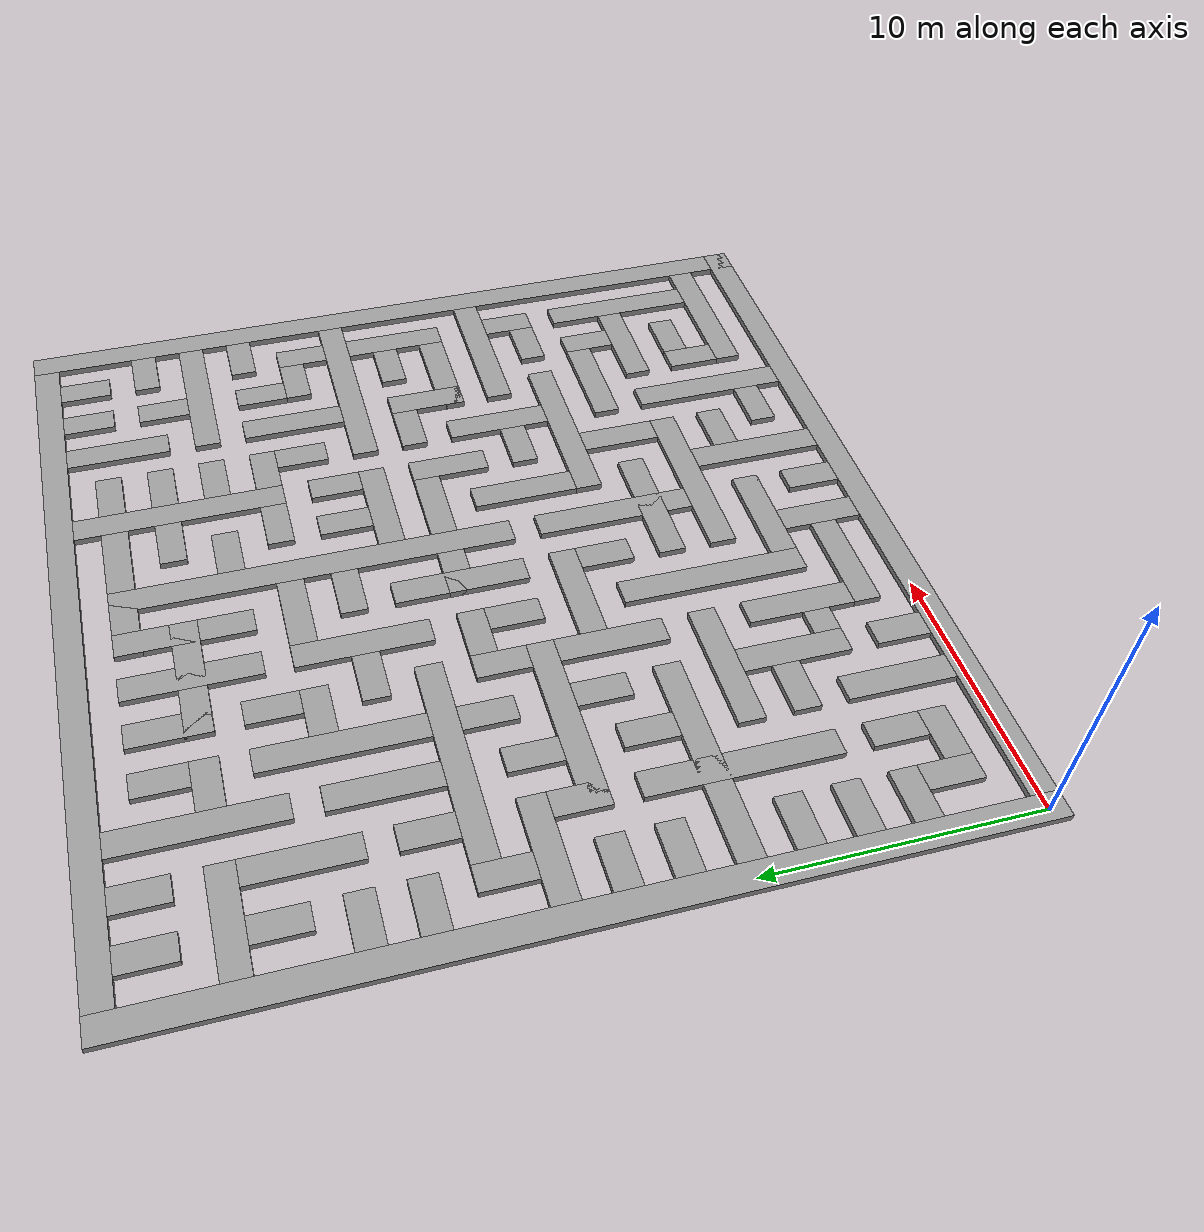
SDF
<?xml version='1.0'?>
<sdf version='1.7'>
  <model name='medium_maze'>
    <pose>15 15 0 0 -0 0</pose>
    <link name='Wall_0'>
      <collision name='Wall_0_Collision'>
        <geometry>
          <box>
            <size>31 1 0.25</size>
          </box>
        </geometry>
        <pose>0 0 0.125 0 -0 0</pose>
      </collision>
      <visual name='Wall_0_Visual'>
        <pose>0 0 0.125 0 -0 0</pose>
        <geometry>
          <box>
            <size>31 1 0.25</size>
          </box>
        </geometry>
        <material>
          <script>
            <uri>file://media/materials/scripts/gazebo.material</uri>
            <name>Gazebo/Grey</name>
          </script>
          <ambient>1 1 1 1</ambient>
        </material>
        <meta>
          <layer>0</layer>
        </meta>
      </visual>
      <pose>-15 0 0 0 -0 1.5708</pose>
    </link>
    <link name='Wall_10'>
      <collision name='Wall_10_Collision'>
        <geometry>
          <box>
            <size>2 1 0.25</size>
          </box>
        </geometry>
        <pose>0 0 0.125 0 -0 0</pose>
      </collision>
      <visual name='Wall_10_Visual'>
        <pose>0 0 0.125 0 -0 0</pose>
        <geometry>
          <box>
            <size>2 1 0.25</size>
          </box>
        </geometry>
        <material>
          <script>
            <uri>file://media/materials/scripts/gazebo.material</uri>
            <name>Gazebo/Grey</name>
          </script>
          <ambient>1 1 1 1</ambient>
        </material>
        <meta>
          <layer>0</layer>
        </meta>
      </visual>
      <pose>-11 13.5 0 0 -0 -1.5708</pose>
    </link>
    <link name='Wall_100'>
      <collision name='Wall_100_Collision'>
        <geometry>
          <box>
            <size>1 1 0.25</size>
          </box>
        </geometry>
        <pose>0 0 0.125 0 -0 0</pose>
      </collision>
      <visual name='Wall_100_Visual'>
        <pose>0 0 0.125 0 -0 0</pose>
        <geometry>
          <box>
            <size>1 1 0.25</size>
          </box>
        </geometry>
        <material>
          <script>
            <uri>file://media/materials/scripts/gazebo.material</uri>
            <name>Gazebo/Grey</name>
          </script>
          <ambient>1 1 1 1</ambient>
        </material>
        <meta>
          <layer>0</layer>
        </meta>
      </visual>
      <pose>1 -11 0 0 -0 0</pose>
    </link>
    <link name='Wall_102'>
      <collision name='Wall_102_Collision'>
        <geometry>
          <box>
            <size>4 1 0.25</size>
          </box>
        </geometry>
        <pose>0 0 0.125 0 -0 0</pose>
      </collision>
      <visual name='Wall_102_Visual'>
        <pose>0 0 0.125 0 -0 0</pose>
        <geometry>
          <box>
            <size>4 1 0.25</size>
          </box>
        </geometry>
        <material>
          <script>
            <uri>file://media/materials/scripts/gazebo.material</uri>
            <name>Gazebo/Grey</name>
          </script>
          <ambient>1 1 1 1</ambient>
        </material>
        <meta>
          <layer>0</layer>
        </meta>
      </visual>
      <pose>-3.5 -13 0 0 -0 0</pose>
    </link>
    <link name='Wall_104'>
      <collision name='Wall_104_Collision'>
        <geometry>
          <box>
            <size>4 1 0.25</size>
          </box>
        </geometry>
        <pose>0 0 0.125 0 -0 0</pose>
      </collision>
      <visual name='Wall_104_Visual'>
        <pose>0 0 0.125 0 -0 0</pose>
        <geometry>
          <box>
            <size>4 1 0.25</size>
          </box>
        </geometry>
        <material>
          <script>
            <uri>file://media/materials/scripts/gazebo.material</uri>
            <name>Gazebo/Grey</name>
          </script>
          <ambient>1 1 1 1</ambient>
        </material>
        <meta>
          <layer>0</layer>
        </meta>
      </visual>
      <pose>-5 -10.5 0 0 -0 -1.5708</pose>
    </link>
    <link name='Wall_106'>
      <collision name='Wall_106_Collision'>
        <geometry>
          <box>
            <size>2 1 0.25</size>
          </box>
        </geometry>
        <pose>0 0 0.125 0 -0 0</pose>
      </collision>
      <visual name='Wall_106_Visual'>
        <pose>0 0 0.125 0 -0 0</pose>
        <geometry>
          <box>
            <size>2 1 0.25</size>
          </box>
        </geometry>
        <material>
          <script>
            <uri>file://media/materials/scripts/gazebo.material</uri>
            <name>Gazebo/Grey</name>
          </script>
          <ambient>1 1 1 1</ambient>
        </material>
        <meta>
          <layer>0</layer>
        </meta>
      </visual>
      <pose>-8.5 -9 0 0 -0 0</pose>
    </link>
    <link name='Wall_108'>
      <collision name='Wall_108_Collision'>
        <geometry>
          <box>
            <size>7 1 0.25</size>
          </box>
        </geometry>
        <pose>0 0 0.125 0 -0 0</pose>
      </collision>
      <visual name='Wall_108_Visual'>
        <pose>0 0 0.125 0 -0 0</pose>
        <geometry>
          <box>
            <size>7 1 0.25</size>
          </box>
        </geometry>
        <material>
          <script>
            <uri>file://media/materials/scripts/gazebo.material</uri>
            <name>Gazebo/Grey</name>
          </script>
          <ambient>1 1 1 1</ambient>
        </material>
        <meta>
          <layer>0</layer>
        </meta>
      </visual>
      <pose>-3 -8 0 0 -0 1.5708</pose>
    </link>
    <link name='Wall_110'>
      <collision name='Wall_110_Collision'>
        <geometry>
          <box>
            <size>2 1 0.25</size>
          </box>
        </geometry>
        <pose>0 0 0.125 0 -0 0</pose>
      </collision>
      <visual name='Wall_110_Visual'>
        <pose>0 0 0.125 0 -0 0</pose>
        <geometry>
          <box>
            <size>2 1 0.25</size>
          </box>
        </geometry>
        <material>
          <script>
            <uri>file://media/materials/scripts/gazebo.material</uri>
            <name>Gazebo/Grey</name>
          </script>
          <ambient>1 1 1 1</ambient>
        </material>
        <meta>
          <layer>0</layer>
        </meta>
      </visual>
      <pose>1 -13.5 0 0 -0 1.5708</pose>
    </link>
    <link name='Wall_112'>
      <collision name='Wall_112_Collision'>
        <geometry>
          <box>
            <size>5 1 0.25</size>
          </box>
        </geometry>
        <pose>0 0 0.125 0 -0 0</pose>
      </collision>
      <visual name='Wall_112_Visual'>
        <pose>0 0 0.125 0 -0 0</pose>
        <geometry>
          <box>
            <size>5 1 0.25</size>
          </box>
        </geometry>
        <material>
          <script>
            <uri>file://media/materials/scripts/gazebo.material</uri>
            <name>Gazebo/Grey</name>
          </script>
          <ambient>1 1 1 1</ambient>
        </material>
        <meta>
          <layer>0</layer>
        </meta>
      </visual>
      <pose>3 -12 0 0 -0 1.5708</pose>
    </link>
    <link name='Wall_114'>
      <collision name='Wall_114_Collision'>
        <geometry>
          <box>
            <size>2 1 0.25</size>
          </box>
        </geometry>
        <pose>0 0 0.125 0 -0 0</pose>
      </collision>
      <visual name='Wall_114_Visual'>
        <pose>0 0 0.125 0 -0 0</pose>
        <geometry>
          <box>
            <size>2 1 0.25</size>
          </box>
        </geometry>
        <material>
          <script>
            <uri>file://media/materials/scripts/gazebo.material</uri>
            <name>Gazebo/Grey</name>
          </script>
          <ambient>1 1 1 1</ambient>
        </material>
        <meta>
          <layer>0</layer>
        </meta>
      </visual>
      <pose>4.5 -11 0 0 -0 0</pose>
    </link>
    <link name='Wall_116'>
      <collision name='Wall_116_Collision'>
        <geometry>
          <box>
            <size>7 1 0.25</size>
          </box>
        </geometry>
        <pose>0 0 0.125 0 -0 0</pose>
      </collision>
      <visual name='Wall_116_Visual'>
        <pose>0 0 0.125 0 -0 0</pose>
        <geometry>
          <box>
            <size>7 1 0.25</size>
          </box>
        </geometry>
        <material>
          <script>
            <uri>file://media/materials/scripts/gazebo.material</uri>
            <name>Gazebo/Grey</name>
          </script>
          <ambient>1 1 1 1</ambient>
        </material>
        <meta>
          <layer>0</layer>
        </meta>
      </visual>
      <pose>2 -9 0 0 -0 0</pose>
    </link>
    <link name='Wall_118'>
      <collision name='Wall_118_Collision'>
        <geometry>
          <box>
            <size>6 1 0.25</size>
          </box>
        </geometry>
        <pose>0 0 0.125 0 -0 0</pose>
      </collision>
      <visual name='Wall_118_Visual'>
        <pose>0 0 0.125 0 -0 0</pose>
        <geometry>
          <box>
            <size>6 1 0.25</size>
          </box>
        </geometry>
        <material>
          <script>
            <uri>file://media/materials/scripts/gazebo.material</uri>
            <name>Gazebo/Grey</name>
          </script>
          <ambient>1 1 1 1</ambient>
        </material>
        <meta>
          <layer>0</layer>
        </meta>
      </visual>
      <pose>1 -5.5 0 0 -0 1.5708</pose>
    </link>
    <link name='Wall_12'>
      <collision name='Wall_12_Collision'>
        <geometry>
          <box>
            <size>6 1 0.25</size>
          </box>
        </geometry>
        <pose>0 0 0.125 0 -0 0</pose>
      </collision>
      <visual name='Wall_12_Visual'>
        <pose>0 0 0.125 0 -0 0</pose>
        <geometry>
          <box>
            <size>6 1 0.25</size>
          </box>
        </geometry>
        <material>
          <script>
            <uri>file://media/materials/scripts/gazebo.material</uri>
            <name>Gazebo/Grey</name>
          </script>
          <ambient>1 1 1 1</ambient>
        </material>
        <meta>
          <layer>0</layer>
        </meta>
      </visual>
      <pose>-9 11.5 0 0 -0 -1.5708</pose>
    </link>
    <link name='Wall_120'>
      <collision name='Wall_120_Collision'>
        <geometry>
          <box>
            <size>4 1 0.25</size>
          </box>
        </geometry>
        <pose>0 0 0.125 0 -0 0</pose>
      </collision>
      <visual name='Wall_120_Visual'>
        <pose>0 0 0.125 0 -0 0</pose>
        <geometry>
          <box>
            <size>4 1 0.25</size>
          </box>
        </geometry>
        <material>
          <script>
            <uri>file://media/materials/scripts/gazebo.material</uri>
            <name>Gazebo/Grey</name>
          </script>
          <ambient>1 1 1 1</ambient>
        </material>
        <meta>
          <layer>0</layer>
        </meta>
      </visual>
      <pose>7 -2.5 0 0 -0 1.5708</pose>
    </link>
    <link name='Wall_122'>
      <collision name='Wall_122_Collision'>
        <geometry>
          <box>
            <size>4 1 0.25</size>
          </box>
        </geometry>
        <pose>0 0 0.125 0 -0 0</pose>
      </collision>
      <visual name='Wall_122_Visual'>
        <pose>0 0 0.125 0 -0 0</pose>
        <geometry>
          <box>
            <size>4 1 0.25</size>
          </box>
        </geometry>
        <material>
          <script>
            <uri>file://media/materials/scripts/gazebo.material</uri>
            <name>Gazebo/Grey</name>
          </script>
          <ambient>1 1 1 1</ambient>
        </material>
        <meta>
          <layer>0</layer>
        </meta>
      </visual>
      <pose>3 -2.5 0 0 -0 1.5708</pose>
    </link>
    <link name='Wall_124'>
      <collision name='Wall_124_Collision'>
        <geometry>
          <box>
            <size>5 1 0.25</size>
          </box>
        </geometry>
        <pose>0 0 0.125 0 -0 0</pose>
      </collision>
      <visual name='Wall_124_Visual'>
        <pose>0 0 0.125 0 -0 0</pose>
        <geometry>
          <box>
            <size>5 1 0.25</size>
          </box>
        </geometry>
        <material>
          <script>
            <uri>file://media/materials/scripts/gazebo.material</uri>
            <name>Gazebo/Grey</name>
          </script>
          <ambient>1 1 1 1</ambient>
        </material>
        <meta>
          <layer>0</layer>
        </meta>
      </visual>
      <pose>1 -7 0 0 -0 0</pose>
    </link>
    <link name='Wall_126'>
      <collision name='Wall_126_Collision'>
        <geometry>
          <box>
            <size>6 1 0.25</size>
          </box>
        </geometry>
        <pose>0 0 0.125 0 -0 0</pose>
      </collision>
      <visual name='Wall_126_Visual'>
        <pose>0 0 0.125 0 -0 0</pose>
        <geometry>
          <box>
            <size>6 1 0.25</size>
          </box>
        </geometry>
        <material>
          <script>
            <uri>file://media/materials/scripts/gazebo.material</uri>
            <name>Gazebo/Grey</name>
          </script>
          <ambient>1 1 1 1</ambient>
        </material>
        <meta>
          <layer>0</layer>
        </meta>
      </visual>
      <pose>11.5 -13 0 0 -0 3.14159</pose>
    </link>
    <link name='Wall_128'>
      <collision name='Wall_128_Collision'>
        <geometry>
          <box>
            <size>6 1 0.25</size>
          </box>
        </geometry>
        <pose>0 0 0.125 0 -0 0</pose>
      </collision>
      <visual name='Wall_128_Visual'>
        <pose>0 0 0.125 0 -0 0</pose>
        <geometry>
          <box>
            <size>6 1 0.25</size>
          </box>
        </geometry>
        <material>
          <script>
            <uri>file://media/materials/scripts/gazebo.material</uri>
            <name>Gazebo/Grey</name>
          </script>
          <ambient>1 1 1 1</ambient>
        </material>
        <meta>
          <layer>0</layer>
        </meta>
      </visual>
      <pose>7 -11.5 0 0 -0 1.5708</pose>
    </link>
    <link name='Wall_130'>
      <collision name='Wall_130_Collision'>
        <geometry>
          <box>
            <size>3 1 0.25</size>
          </box>
        </geometry>
        <pose>0 0 0.125 0 -0 0</pose>
      </collision>
      <visual name='Wall_130_Visual'>
        <pose>0 0 0.125 0 -0 0</pose>
        <geometry>
          <box>
            <size>3 1 0.25</size>
          </box>
        </geometry>
        <material>
          <script>
            <uri>file://media/materials/scripts/gazebo.material</uri>
            <name>Gazebo/Grey</name>
          </script>
          <ambient>1 1 1 1</ambient>
        </material>
        <meta>
          <layer>0</layer>
        </meta>
      </visual>
      <pose>5 -7 0 0 -0 1.5708</pose>
    </link>
    <link name='Wall_132'>
      <collision name='Wall_132_Collision'>
        <geometry>
          <box>
            <size>2 1 0.25</size>
          </box>
        </geometry>
        <pose>0 0 0.125 0 -0 0</pose>
      </collision>
      <visual name='Wall_132_Visual'>
        <pose>0 0 0.125 0 -0 0</pose>
        <geometry>
          <box>
            <size>2 1 0.25</size>
          </box>
        </geometry>
        <material>
          <script>
            <uri>file://media/materials/scripts/gazebo.material</uri>
            <name>Gazebo/Grey</name>
          </script>
          <ambient>1 1 1 1</ambient>
        </material>
        <meta>
          <layer>0</layer>
        </meta>
      </visual>
      <pose>10.5 -11 0 0 -0 0</pose>
    </link>
    <link name='Wall_134'>
      <collision name='Wall_134_Collision'>
        <geometry>
          <box>
            <size>2 1 0.25</size>
          </box>
        </geometry>
        <pose>0 0 0.125 0 -0 0</pose>
      </collision>
      <visual name='Wall_134_Visual'>
        <pose>0 0 0.125 0 -0 0</pose>
        <geometry>
          <box>
            <size>2 1 0.25</size>
          </box>
        </geometry>
        <material>
          <script>
            <uri>file://media/materials/scripts/gazebo.material</uri>
            <name>Gazebo/Grey</name>
          </script>
          <ambient>1 1 1 1</ambient>
        </material>
        <meta>
          <layer>0</layer>
        </meta>
      </visual>
      <pose>9 -11.5 0 0 -0 1.5708</pose>
    </link>
    <link name='Wall_136'>
      <collision name='Wall_136_Collision'>
        <geometry>
          <box>
            <size>2 1 0.25</size>
          </box>
        </geometry>
        <pose>0 0 0.125 0 -0 0</pose>
      </collision>
      <visual name='Wall_136_Visual'>
        <pose>0 0 0.125 0 -0 0</pose>
        <geometry>
          <box>
            <size>2 1 0.25</size>
          </box>
        </geometry>
        <material>
          <script>
            <uri>file://media/materials/scripts/gazebo.material</uri>
            <name>Gazebo/Grey</name>
          </script>
          <ambient>1 1 1 1</ambient>
        </material>
        <meta>
          <layer>0</layer>
        </meta>
      </visual>
      <pose>5.5 -3 0 0 -0 3.14159</pose>
    </link>
    <link name='Wall_138'>
      <collision name='Wall_138_Collision'>
        <geometry>
          <box>
            <size>7 1 0.25</size>
          </box>
        </geometry>
        <pose>0 0 0.125 0 -0 0</pose>
      </collision>
      <visual name='Wall_138_Visual'>
        <pose>0 0 0.125 0 -0 0</pose>
        <geometry>
          <box>
            <size>7 1 0.25</size>
          </box>
        </geometry>
        <material>
          <script>
            <uri>file://media/materials/scripts/gazebo.material</uri>
            <name>Gazebo/Grey</name>
          </script>
          <ambient>1 1 1 1</ambient>
        </material>
        <meta>
          <layer>0</layer>
        </meta>
      </visual>
      <pose>6 -5 0 0 -0 0</pose>
    </link>
    <link name='Wall_14'>
      <collision name='Wall_14_Collision'>
        <geometry>
          <box>
            <size>2 1 0.25</size>
          </box>
        </geometry>
        <pose>0 0 0.125 0 -0 0</pose>
      </collision>
      <visual name='Wall_14_Visual'>
        <pose>0 0 0.125 0 -0 0</pose>
        <geometry>
          <box>
            <size>2 1 0.25</size>
          </box>
        </geometry>
        <material>
          <script>
            <uri>file://media/materials/scripts/gazebo.material</uri>
            <name>Gazebo/Grey</name>
          </script>
          <ambient>1 1 1 1</ambient>
        </material>
        <meta>
          <layer>0</layer>
        </meta>
      </visual>
      <pose>-7.5 11 0 0 -0 0</pose>
    </link>
    <link name='Wall_140'>
      <collision name='Wall_140_Collision'>
        <geometry>
          <box>
            <size>2 1 0.25</size>
          </box>
        </geometry>
        <pose>0 0 0.125 0 -0 0</pose>
      </collision>
      <visual name='Wall_140_Visual'>
        <pose>0 0 0.125 0 -0 0</pose>
        <geometry>
          <box>
            <size>2 1 0.25</size>
          </box>
        </geometry>
        <material>
          <script>
            <uri>file://media/materials/scripts/gazebo.material</uri>
            <name>Gazebo/Grey</name>
          </script>
          <ambient>1 1 1 1</ambient>
        </material>
        <meta>
          <layer>0</layer>
        </meta>
      </visual>
      <pose>5.5 -13 0 0 -0 3.14159</pose>
    </link>
    <link name='Wall_142'>
      <collision name='Wall_142_Collision'>
        <geometry>
          <box>
            <size>4 1 0.25</size>
          </box>
        </geometry>
        <pose>0 0 0.125 0 -0 0</pose>
      </collision>
      <visual name='Wall_142_Visual'>
        <pose>0 0 0.125 0 -0 0</pose>
        <geometry>
          <box>
            <size>4 1 0.25</size>
          </box>
        </geometry>
        <material>
          <script>
            <uri>file://media/materials/scripts/gazebo.material</uri>
            <name>Gazebo/Grey</name>
          </script>
          <ambient>1 1 1 1</ambient>
        </material>
        <meta>
          <layer>0</layer>
        </meta>
      </visual>
      <pose>10.5 -9 0 0 -0 3.14159</pose>
    </link>
    <link name='Wall_144'>
      <collision name='Wall_144_Collision'>
        <geometry>
          <box>
            <size>2 1 0.25</size>
          </box>
        </geometry>
        <pose>0 0 0.125 0 -0 0</pose>
      </collision>
      <visual name='Wall_144_Visual'>
        <pose>0 0 0.125 0 -0 0</pose>
        <geometry>
          <box>
            <size>2 1 0.25</size>
          </box>
        </geometry>
        <material>
          <script>
            <uri>file://media/materials/scripts/gazebo.material</uri>
            <name>Gazebo/Grey</name>
          </script>
          <ambient>1 1 1 1</ambient>
        </material>
        <meta>
          <layer>0</layer>
        </meta>
      </visual>
      <pose>11.5 -5 0 0 -0 0</pose>
    </link>
    <link name='Wall_146'>
      <collision name='Wall_146_Collision'>
        <geometry>
          <box>
            <size>6 1 0.25</size>
          </box>
        </geometry>
        <pose>0 0 0.125 0 -0 0</pose>
      </collision>
      <visual name='Wall_146_Visual'>
        <pose>0 0 0.125 0 -0 0</pose>
        <geometry>
          <box>
            <size>6 1 0.25</size>
          </box>
        </geometry>
        <material>
          <script>
            <uri>file://media/materials/scripts/gazebo.material</uri>
            <name>Gazebo/Grey</name>
          </script>
          <ambient>1 1 1 1</ambient>
        </material>
        <meta>
          <layer>0</layer>
        </meta>
      </visual>
      <pose>11.5 -3 0 0 -0 3.14159</pose>
    </link>
    <link name='Wall_148'>
      <collision name='Wall_148_Collision'>
        <geometry>
          <box>
            <size>4 1 0.25</size>
          </box>
        </geometry>
        <pose>0 0 0.125 0 -0 0</pose>
      </collision>
      <visual name='Wall_148_Visual'>
        <pose>0 0 0.125 0 -0 0</pose>
        <geometry>
          <box>
            <size>4 1 0.25</size>
          </box>
        </geometry>
        <material>
          <script>
            <uri>file://media/materials/scripts/gazebo.material</uri>
            <name>Gazebo/Grey</name>
          </script>
          <ambient>1 1 1 1</ambient>
        </material>
        <meta>
          <layer>0</layer>
        </meta>
      </visual>
      <pose>8.5 -7 0 0 -0 3.14159</pose>
    </link>
    <link name='Wall_150'>
      <collision name='Wall_150_Collision'>
        <geometry>
          <box>
            <size>2 1 0.25</size>
          </box>
        </geometry>
        <pose>0 0 0.125 0 -0 0</pose>
      </collision>
      <visual name='Wall_150_Visual'>
        <pose>0 0 0.125 0 -0 0</pose>
        <geometry>
          <box>
            <size>2 1 0.25</size>
          </box>
        </geometry>
        <material>
          <script>
            <uri>file://media/materials/scripts/gazebo.material</uri>
            <name>Gazebo/Grey</name>
          </script>
          <ambient>1 1 1 1</ambient>
        </material>
        <meta>
          <layer>0</layer>
        </meta>
      </visual>
      <pose>13 -4.5 0 0 -0 1.5708</pose>
    </link>
    <link name='Wall_152'>
      <collision name='Wall_152_Collision'>
        <geometry>
          <box>
            <size>8 1 0.25</size>
          </box>
        </geometry>
        <pose>0 0 0.125 0 -0 0</pose>
      </collision>
      <visual name='Wall_152_Visual'>
        <pose>0 0 0.125 0 -0 0</pose>
        <geometry>
          <box>
            <size>8 1 0.25</size>
          </box>
        </geometry>
        <material>
          <script>
            <uri>file://media/materials/scripts/gazebo.material</uri>
            <name>Gazebo/Grey</name>
          </script>
          <ambient>1 1 1 1</ambient>
        </material>
        <meta>
          <layer>0</layer>
        </meta>
      </visual>
      <pose>10.5 3 0 0 -0 3.14159</pose>
    </link>
    <link name='Wall_154'>
      <collision name='Wall_154_Collision'>
        <geometry>
          <box>
            <size>7 1 0.25</size>
          </box>
        </geometry>
        <pose>0 0 0.125 0 -0 0</pose>
      </collision>
      <visual name='Wall_154_Visual'>
        <pose>0 0 0.125 0 -0 0</pose>
        <geometry>
          <box>
            <size>7 1 0.25</size>
          </box>
        </geometry>
        <material>
          <script>
            <uri>file://media/materials/scripts/gazebo.material</uri>
            <name>Gazebo/Grey</name>
          </script>
          <ambient>1 1 1 1</ambient>
        </material>
        <meta>
          <layer>0</layer>
        </meta>
      </visual>
      <pose>13 2 0 0 -0 1.5708</pose>
    </link>
    <link name='Wall_156'>
      <collision name='Wall_156_Collision'>
        <geometry>
          <box>
            <size>2 1 0.25</size>
          </box>
        </geometry>
        <pose>0 0 0.125 0 -0 0</pose>
      </collision>
      <visual name='Wall_156_Visual'>
        <pose>0 0 0.125 0 -0 0</pose>
        <geometry>
          <box>
            <size>2 1 0.25</size>
          </box>
        </geometry>
        <material>
          <script>
            <uri>file://media/materials/scripts/gazebo.material</uri>
            <name>Gazebo/Grey</name>
          </script>
          <ambient>1 1 1 1</ambient>
        </material>
        <meta>
          <layer>0</layer>
        </meta>
      </visual>
      <pose>11.5 5 0 0 -0 3.14159</pose>
    </link>
    <link name='Wall_158'>
      <collision name='Wall_158_Collision'>
        <geometry>
          <box>
            <size>2 1 0.25</size>
          </box>
        </geometry>
        <pose>0 0 0.125 0 -0 0</pose>
      </collision>
      <visual name='Wall_158_Visual'>
        <pose>0 0 0.125 0 -0 0</pose>
        <geometry>
          <box>
            <size>2 1 0.25</size>
          </box>
        </geometry>
        <material>
          <script>
            <uri>file://media/materials/scripts/gazebo.material</uri>
            <name>Gazebo/Grey</name>
          </script>
          <ambient>1 1 1 1</ambient>
        </material>
        <meta>
          <layer>0</layer>
        </meta>
      </visual>
      <pose>11 -7.5 0 0 -0 -1.5708</pose>
    </link>
    <link name='Wall_16'>
      <collision name='Wall_16_Collision'>
        <geometry>
          <box>
            <size>2 1 0.25</size>
          </box>
        </geometry>
        <pose>0 0 0.125 0 -0 0</pose>
      </collision>
      <visual name='Wall_16_Visual'>
        <pose>0 0 0.125 0 -0 0</pose>
        <geometry>
          <box>
            <size>2 1 0.25</size>
          </box>
        </geometry>
        <material>
          <script>
            <uri>file://media/materials/scripts/gazebo.material</uri>
            <name>Gazebo/Grey</name>
          </script>
          <ambient>1 1 1 1</ambient>
        </material>
        <meta>
          <layer>0</layer>
        </meta>
      </visual>
      <pose>-7 12.5 0 0 -0 1.5708</pose>
    </link>
    <link name='Wall_160'>
      <collision name='Wall_160_Collision'>
        <geometry>
          <box>
            <size>3 1 0.25</size>
          </box>
        </geometry>
        <pose>0 0 0.125 0 -0 0</pose>
      </collision>
      <visual name='Wall_160_Visual'>
        <pose>0 0 0.125 0 -0 0</pose>
        <geometry>
          <box>
            <size>3 1 0.25</size>
          </box>
        </geometry>
        <material>
          <script>
            <uri>file://media/materials/scripts/gazebo.material</uri>
            <name>Gazebo/Grey</name>
          </script>
          <ambient>1 1 1 1</ambient>
        </material>
        <meta>
          <layer>0</layer>
        </meta>
      </visual>
      <pose>9 0 0 0 -0 1.5708</pose>
    </link>
    <link name='Wall_162'>
      <collision name='Wall_162_Collision'>
        <geometry>
          <box>
            <size>2 1 0.25</size>
          </box>
        </geometry>
        <pose>0 0 0.125 0 -0 0</pose>
      </collision>
      <visual name='Wall_162_Visual'>
        <pose>0 0 0.125 0 -0 0</pose>
        <geometry>
          <box>
            <size>2 1 0.25</size>
          </box>
        </geometry>
        <material>
          <script>
            <uri>file://media/materials/scripts/gazebo.material</uri>
            <name>Gazebo/Grey</name>
          </script>
          <ambient>1 1 1 1</ambient>
        </material>
        <meta>
          <layer>0</layer>
        </meta>
      </visual>
      <pose>11 6.5 0 0 -0 1.5708</pose>
    </link>
    <link name='Wall_164'>
      <collision name='Wall_164_Collision'>
        <geometry>
          <box>
            <size>4 1 0.25</size>
          </box>
        </geometry>
        <pose>0 0 0.125 0 -0 0</pose>
      </collision>
      <visual name='Wall_164_Visual'>
        <pose>0 0 0.125 0 -0 0</pose>
        <geometry>
          <box>
            <size>4 1 0.25</size>
          </box>
        </geometry>
        <material>
          <script>
            <uri>file://media/materials/scripts/gazebo.material</uri>
            <name>Gazebo/Grey</name>
          </script>
          <ambient>1 1 1 1</ambient>
        </material>
        <meta>
          <layer>0</layer>
        </meta>
      </visual>
      <pose>9 5.5 0 0 -0 1.5708</pose>
    </link>
    <link name='Wall_166'>
      <collision name='Wall_166_Collision'>
        <geometry>
          <box>
            <size>4 1 0.25</size>
          </box>
        </geometry>
        <pose>0 0 0.125 0 -0 0</pose>
      </collision>
      <visual name='Wall_166_Visual'>
        <pose>0 0 0.125 0 -0 0</pose>
        <geometry>
          <box>
            <size>4 1 0.25</size>
          </box>
        </geometry>
        <material>
          <script>
            <uri>file://media/materials/scripts/gazebo.material</uri>
            <name>Gazebo/Grey</name>
          </script>
          <ambient>1 1 1 1</ambient>
        </material>
        <meta>
          <layer>0</layer>
        </meta>
      </visual>
      <pose>10.5 -1 0 0 -0 3.14159</pose>
    </link>
    <link name='Wall_168'>
      <collision name='Wall_168_Collision'>
        <geometry>
          <box>
            <size>2 1 0.25</size>
          </box>
        </geometry>
        <pose>0 0 0.125 0 -0 0</pose>
      </collision>
      <visual name='Wall_168_Visual'>
        <pose>0 0 0.125 0 -0 0</pose>
        <geometry>
          <box>
            <size>2 1 0.25</size>
          </box>
        </geometry>
        <material>
          <script>
            <uri>file://media/materials/scripts/gazebo.material</uri>
            <name>Gazebo/Grey</name>
          </script>
          <ambient>1 1 1 1</ambient>
        </material>
        <meta>
          <layer>0</layer>
        </meta>
      </visual>
      <pose>7.5 1 0 0 -0 3.14159</pose>
    </link>
    <link name='Wall_170'>
      <collision name='Wall_170_Collision'>
        <geometry>
          <box>
            <size>6 1 0.25</size>
          </box>
        </geometry>
        <pose>0 0 0.125 0 -0 0</pose>
      </collision>
      <visual name='Wall_170_Visual'>
        <pose>0 0 0.125 0 -0 0</pose>
        <geometry>
          <box>
            <size>6 1 0.25</size>
          </box>
        </geometry>
        <material>
          <script>
            <uri>file://media/materials/scripts/gazebo.material</uri>
            <name>Gazebo/Grey</name>
          </script>
          <ambient>1 1 1 1</ambient>
        </material>
        <meta>
          <layer>0</layer>
        </meta>
      </visual>
      <pose>13 -9.5 0 0 -0 1.5708</pose>
    </link>
    <link name='Wall_172'>
      <collision name='Wall_172_Collision'>
        <geometry>
          <box>
            <size>4 1 0.25</size>
          </box>
        </geometry>
        <pose>0 0 0.125 0 -0 0</pose>
      </collision>
      <visual name='Wall_172_Visual'>
        <pose>0 0 0.125 0 -0 0</pose>
        <geometry>
          <box>
            <size>4 1 0.25</size>
          </box>
        </geometry>
        <material>
          <script>
            <uri>file://media/materials/scripts/gazebo.material</uri>
            <name>Gazebo/Grey</name>
          </script>
          <ambient>1 1 1 1</ambient>
        </material>
        <meta>
          <layer>0</layer>
        </meta>
      </visual>
      <pose>9 12.5 0 0 -0 -1.5708</pose>
    </link>
    <link name='Wall_174'>
      <collision name='Wall_174_Collision'>
        <geometry>
          <box>
            <size>2 1 0.25</size>
          </box>
        </geometry>
        <pose>0 0 0.125 0 -0 0</pose>
      </collision>
      <visual name='Wall_174_Visual'>
        <pose>0 0 0.125 0 -0 0</pose>
        <geometry>
          <box>
            <size>2 1 0.25</size>
          </box>
        </geometry>
        <material>
          <script>
            <uri>file://media/materials/scripts/gazebo.material</uri>
            <name>Gazebo/Grey</name>
          </script>
          <ambient>1 1 1 1</ambient>
        </material>
        <meta>
          <layer>0</layer>
        </meta>
      </visual>
      <pose>11 13.5 0 0 -0 -1.5708</pose>
    </link>
    <link name='Wall_176'>
      <collision name='Wall_176_Collision'>
        <geometry>
          <box>
            <size>2 1 0.25</size>
          </box>
        </geometry>
        <pose>0 0 0.125 0 -0 0</pose>
      </collision>
      <visual name='Wall_176_Visual'>
        <pose>0 0 0.125 0 -0 0</pose>
        <geometry>
          <box>
            <size>2 1 0.25</size>
          </box>
        </geometry>
        <material>
          <script>
            <uri>file://media/materials/scripts/gazebo.material</uri>
            <name>Gazebo/Grey</name>
          </script>
          <ambient>1 1 1 1</ambient>
        </material>
        <meta>
          <layer>0</layer>
        </meta>
      </visual>
      <pose>13 13.5 0 0 -0 -1.5708</pose>
    </link>
    <link name='Wall_178'>
      <collision name='Wall_178_Collision'>
        <geometry>
          <box>
            <size>2 1 0.25</size>
          </box>
        </geometry>
        <pose>0 0 0.125 0 -0 0</pose>
      </collision>
      <visual name='Wall_178_Visual'>
        <pose>0 0 0.125 0 -0 0</pose>
        <geometry>
          <box>
            <size>2 1 0.25</size>
          </box>
        </geometry>
        <material>
          <script>
            <uri>file://media/materials/scripts/gazebo.material</uri>
            <name>Gazebo/Grey</name>
          </script>
          <ambient>1 1 1 1</ambient>
        </material>
        <meta>
          <layer>0</layer>
        </meta>
      </visual>
      <pose>13.5 11 0 0 -0 3.14159</pose>
    </link>
    <link name='Wall_18'>
      <collision name='Wall_18_Collision'>
        <geometry>
          <box>
            <size>4 1 0.25</size>
          </box>
        </geometry>
        <pose>0 0 0.125 0 -0 0</pose>
      </collision>
      <visual name='Wall_18_Visual'>
        <pose>0 0 0.125 0 -0 0</pose>
        <geometry>
          <box>
            <size>4 1 0.25</size>
          </box>
        </geometry>
        <material>
          <script>
            <uri>file://media/materials/scripts/gazebo.material</uri>
            <name>Gazebo/Grey</name>
          </script>
          <ambient>1 1 1 1</ambient>
        </material>
        <meta>
          <layer>0</layer>
        </meta>
      </visual>
      <pose>-12.5 11 0 0 -0 0</pose>
    </link>
    <link name='Wall_180'>
      <collision name='Wall_180_Collision'>
        <geometry>
          <box>
            <size>2 1 0.25</size>
          </box>
        </geometry>
        <pose>0 0 0.125 0 -0 0</pose>
      </collision>
      <visual name='Wall_180_Visual'>
        <pose>0 0 0.125 0 -0 0</pose>
        <geometry>
          <box>
            <size>2 1 0.25</size>
          </box>
        </geometry>
        <material>
          <script>
            <uri>file://media/materials/scripts/gazebo.material</uri>
            <name>Gazebo/Grey</name>
          </script>
          <ambient>1 1 1 1</ambient>
        </material>
        <meta>
          <layer>0</layer>
        </meta>
      </visual>
      <pose>13.5 7 0 0 -0 3.14159</pose>
    </link>
    <link name='Wall_182'>
      <collision name='Wall_182_Collision'>
        <geometry>
          <box>
            <size>6 1 0.25</size>
          </box>
        </geometry>
        <pose>0 0 0.125 0 -0 0</pose>
      </collision>
      <visual name='Wall_182_Visual'>
        <pose>0 0 0.125 0 -0 0</pose>
        <geometry>
          <box>
            <size>6 1 0.25</size>
          </box>
        </geometry>
        <material>
          <script>
            <uri>file://media/materials/scripts/gazebo.material</uri>
            <name>Gazebo/Grey</name>
          </script>
          <ambient>1 1 1 1</ambient>
        </material>
        <meta>
          <layer>0</layer>
        </meta>
      </visual>
      <pose>11.5 9 0 0 -0 3.14159</pose>
    </link>
    <link name='Wall_184'>
      <collision name='Wall_184_Collision'>
        <geometry>
          <box>
            <size>8 1 0.25</size>
          </box>
        </geometry>
        <pose>0 0 0.125 0 -0 0</pose>
      </collision>
      <visual name='Wall_184_Visual'>
        <pose>0 0 0.125 0 -0 0</pose>
        <geometry>
          <box>
            <size>8 1 0.25</size>
          </box>
        </geometry>
        <material>
          <script>
            <uri>file://media/materials/scripts/gazebo.material</uri>
            <name>Gazebo/Grey</name>
          </script>
          <ambient>1 1 1 1</ambient>
        </material>
        <meta>
          <layer>0</layer>
        </meta>
      </visual>
      <pose>5 10.5 0 0 -0 -1.5708</pose>
    </link>
    <link name='Wall_186'>
      <collision name='Wall_186_Collision'>
        <geometry>
          <box>
            <size>2 1 0.25</size>
          </box>
        </geometry>
        <pose>0 0 0.125 0 -0 0</pose>
      </collision>
      <visual name='Wall_186_Visual'>
        <pose>0 0 0.125 0 -0 0</pose>
        <geometry>
          <box>
            <size>2 1 0.25</size>
          </box>
        </geometry>
        <material>
          <script>
            <uri>file://media/materials/scripts/gazebo.material</uri>
            <name>Gazebo/Grey</name>
          </script>
          <ambient>1 1 1 1</ambient>
        </material>
        <meta>
          <layer>0</layer>
        </meta>
      </visual>
      <pose>6.5 11 0 0 -0 0</pose>
    </link>
    <link name='Wall_188'>
      <collision name='Wall_188_Collision'>
        <geometry>
          <box>
            <size>2 1 0.25</size>
          </box>
        </geometry>
        <pose>0 0 0.125 0 -0 0</pose>
      </collision>
      <visual name='Wall_188_Visual'>
        <pose>0 0 0.125 0 -0 0</pose>
        <geometry>
          <box>
            <size>2 1 0.25</size>
          </box>
        </geometry>
        <material>
          <script>
            <uri>file://media/materials/scripts/gazebo.material</uri>
            <name>Gazebo/Grey</name>
          </script>
          <ambient>1 1 1 1</ambient>
        </material>
        <meta>
          <layer>0</layer>
        </meta>
      </visual>
      <pose>6.5 13 0 0 -0 0</pose>
    </link>
    <link name='Wall_190'>
      <collision name='Wall_190_Collision'>
        <geometry>
          <box>
            <size>2 1 0.25</size>
          </box>
        </geometry>
        <pose>0 0 0.125 0 -0 0</pose>
      </collision>
      <visual name='Wall_190_Visual'>
        <pose>0 0 0.125 0 -0 0</pose>
        <geometry>
          <box>
            <size>2 1 0.25</size>
          </box>
        </geometry>
        <material>
          <script>
            <uri>file://media/materials/scripts/gazebo.material</uri>
            <name>Gazebo/Grey</name>
          </script>
          <ambient>1 1 1 1</ambient>
        </material>
        <meta>
          <layer>0</layer>
        </meta>
      </visual>
      <pose>11 10.5 0 0 -0 1.5708</pose>
    </link>
    <link name='Wall_192'>
      <collision name='Wall_192_Collision'>
        <geometry>
          <box>
            <size>2 1 0.25</size>
          </box>
        </geometry>
        <pose>0 0 0.125 0 -0 0</pose>
      </collision>
      <visual name='Wall_192_Visual'>
        <pose>0 0 0.125 0 -0 0</pose>
        <geometry>
          <box>
            <size>2 1 0.25</size>
          </box>
        </geometry>
        <material>
          <script>
            <uri>file://media/materials/scripts/gazebo.material</uri>
            <name>Gazebo/Grey</name>
          </script>
          <ambient>1 1 1 1</ambient>
        </material>
        <meta>
          <layer>0</layer>
        </meta>
      </visual>
      <pose>6.5 9 0 0 -0 0</pose>
    </link>
    <link name='Wall_194'>
      <collision name='Wall_194_Collision'>
        <geometry>
          <box>
            <size>2 1 0.25</size>
          </box>
        </geometry>
        <pose>0 0 0.125 0 -0 0</pose>
      </collision>
      <visual name='Wall_194_Visual'>
        <pose>0 0 0.125 0 -0 0</pose>
        <geometry>
          <box>
            <size>2 1 0.25</size>
          </box>
        </geometry>
        <material>
          <script>
            <uri>file://media/materials/scripts/gazebo.material</uri>
            <name>Gazebo/Grey</name>
          </script>
          <ambient>1 1 1 1</ambient>
        </material>
        <meta>
          <layer>0</layer>
        </meta>
      </visual>
      <pose>6.5 7 0 0 -0 0</pose>
    </link>
    <link name='Wall_196'>
      <collision name='Wall_196_Collision'>
        <geometry>
          <box>
            <size>2 1 0.25</size>
          </box>
        </geometry>
        <pose>0 0 0.125 0 -0 0</pose>
      </collision>
      <visual name='Wall_196_Visual'>
        <pose>0 0 0.125 0 -0 0</pose>
        <geometry>
          <box>
            <size>2 1 0.25</size>
          </box>
        </geometry>
        <material>
          <script>
            <uri>file://media/materials/scripts/gazebo.material</uri>
            <name>Gazebo/Grey</name>
          </script>
          <ambient>1 1 1 1</ambient>
        </material>
        <meta>
          <layer>0</layer>
        </meta>
      </visual>
      <pose>7 5.5 0 0 -0 -1.5708</pose>
    </link>
    <link name='Wall_198'>
      <collision name='Wall_198_Collision'>
        <geometry>
          <box>
            <size>5 1 0.25</size>
          </box>
        </geometry>
        <pose>0 0 0.125 0 -0 0</pose>
      </collision>
      <visual name='Wall_198_Visual'>
        <pose>0 0 0.125 0 -0 0</pose>
        <geometry>
          <box>
            <size>5 1 0.25</size>
          </box>
        </geometry>
        <material>
          <script>
            <uri>file://media/materials/scripts/gazebo.material</uri>
            <name>Gazebo/Grey</name>
          </script>
          <ambient>1 1 1 1</ambient>
        </material>
        <meta>
          <layer>0</layer>
        </meta>
      </visual>
      <pose>-1 11 0 0 -0 -1.5708</pose>
    </link>
    <link name='Wall_2'>
      <collision name='Wall_2_Collision'>
        <geometry>
          <box>
            <size>30 1 0.25</size>
          </box>
        </geometry>
        <pose>0 0 0.125 0 -0 0</pose>
      </collision>
      <visual name='Wall_2_Visual'>
        <pose>0 0 0.125 0 -0 0</pose>
        <geometry>
          <box>
            <size>30 1 0.25</size>
          </box>
        </geometry>
        <material>
          <script>
            <uri>file://media/materials/scripts/gazebo.material</uri>
            <name>Gazebo/Grey</name>
          </script>
          <ambient>1 1 1 1</ambient>
        </material>
        <meta>
          <layer>0</layer>
        </meta>
      </visual>
      <pose>0.5 -15 0 0 -0 0</pose>
    </link>
    <link name='Wall_20'>
      <collision name='Wall_20_Collision'>
        <geometry>
          <box>
            <size>2 1 0.25</size>
          </box>
        </geometry>
        <pose>0 0 0.125 0 -0 0</pose>
      </collision>
      <visual name='Wall_20_Visual'>
        <pose>0 0 0.125 0 -0 0</pose>
        <geometry>
          <box>
            <size>2 1 0.25</size>
          </box>
        </geometry>
        <material>
          <script>
            <uri>file://media/materials/scripts/gazebo.material</uri>
            <name>Gazebo/Grey</name>
          </script>
          <ambient>1 1 1 1</ambient>
        </material>
        <meta>
          <layer>0</layer>
        </meta>
      </visual>
      <pose>-13 9.5 0 0 -0 -1.5708</pose>
    </link>
    <link name='Wall_200'>
      <collision name='Wall_200_Collision'>
        <geometry>
          <box>
            <size>6 1 0.25</size>
          </box>
        </geometry>
        <pose>0 0 0.125 0 -0 0</pose>
      </collision>
      <visual name='Wall_200_Visual'>
        <pose>0 0 0.125 0 -0 0</pose>
        <geometry>
          <box>
            <size>6 1 0.25</size>
          </box>
        </geometry>
        <material>
          <script>
            <uri>file://media/materials/scripts/gazebo.material</uri>
            <name>Gazebo/Grey</name>
          </script>
          <ambient>1 1 1 1</ambient>
        </material>
        <meta>
          <layer>0</layer>
        </meta>
      </visual>
      <pose>1.5 13 0 0 -0 3.14159</pose>
    </link>
    <link name='Wall_202'>
      <collision name='Wall_202_Collision'>
        <geometry>
          <box>
            <size>2 1 0.25</size>
          </box>
        </geometry>
        <pose>0 0 0.125 0 -0 0</pose>
      </collision>
      <visual name='Wall_202_Visual'>
        <pose>0 0 0.125 0 -0 0</pose>
        <geometry>
          <box>
            <size>2 1 0.25</size>
          </box>
        </geometry>
        <material>
          <script>
            <uri>file://media/materials/scripts/gazebo.material</uri>
            <name>Gazebo/Grey</name>
          </script>
          <ambient>1 1 1 1</ambient>
        </material>
        <meta>
          <layer>0</layer>
        </meta>
      </visual>
      <pose>3.5 7 0 0 -0 3.14159</pose>
    </link>
    <link name='Wall_204'>
      <collision name='Wall_204_Collision'>
        <geometry>
          <box>
            <size>15 1 0.25</size>
          </box>
        </geometry>
        <pose>0 0 0.125 0 -0 0</pose>
      </collision>
      <visual name='Wall_204_Visual'>
        <pose>0 0 0.125 0 -0 0</pose>
        <geometry>
          <box>
            <size>15 1 0.25</size>
          </box>
        </geometry>
        <material>
          <script>
            <uri>file://media/materials/scripts/gazebo.material</uri>
            <name>Gazebo/Grey</name>
          </script>
          <ambient>1 1 1 1</ambient>
        </material>
        <meta>
          <layer>0</layer>
        </meta>
      </visual>
      <pose>1 6 0 0 -0 -1.5708</pose>
    </link>
    <link name='Wall_206'>
      <collision name='Wall_206_Collision'>
        <geometry>
          <box>
            <size>3 1 0.25</size>
          </box>
        </geometry>
        <pose>0 0 0.125 0 -0 0</pose>
      </collision>
      <visual name='Wall_206_Visual'>
        <pose>0 0 0.125 0 -0 0</pose>
        <geometry>
          <box>
            <size>3 1 0.25</size>
          </box>
        </geometry>
        <material>
          <script>
            <uri>file://media/materials/scripts/gazebo.material</uri>
            <name>Gazebo/Grey</name>
          </script>
          <ambient>1 1 1 1</ambient>
        </material>
        <meta>
          <layer>0</layer>
        </meta>
      </visual>
      <pose>5 0 0 0 -0 -1.5708</pose>
    </link>
    <link name='Wall_208'>
      <collision name='Wall_208_Collision'>
        <geometry>
          <box>
            <size>7 1 0.25</size>
          </box>
        </geometry>
        <pose>0 0 0.125 0 -0 0</pose>
      </collision>
      <visual name='Wall_208_Visual'>
        <pose>0 0 0.125 0 -0 0</pose>
        <geometry>
          <box>
            <size>7 1 0.25</size>
          </box>
        </geometry>
        <material>
          <script>
            <uri>file://media/materials/scripts/gazebo.material</uri>
            <name>Gazebo/Grey</name>
          </script>
          <ambient>1 1 1 1</ambient>
        </material>
        <meta>
          <layer>0</layer>
        </meta>
      </visual>
      <pose>2 1 0 0 -0 0</pose>
    </link>
    <link name='Wall_210'>
      <collision name='Wall_210_Collision'>
        <geometry>
          <box>
            <size>2 1 0.25</size>
          </box>
        </geometry>
        <pose>0 0 0.125 0 -0 0</pose>
      </collision>
      <visual name='Wall_210_Visual'>
        <pose>0 0 0.125 0 -0 0</pose>
        <geometry>
          <box>
            <size>2 1 0.25</size>
          </box>
        </geometry>
        <material>
          <script>
            <uri>file://media/materials/scripts/gazebo.material</uri>
            <name>Gazebo/Grey</name>
          </script>
          <ambient>1 1 1 1</ambient>
        </material>
        <meta>
          <layer>0</layer>
        </meta>
      </visual>
      <pose>3.5 11 0 0 -0 3.14159</pose>
    </link>
    <link name='Wall_212'>
      <collision name='Wall_212_Collision'>
        <geometry>
          <box>
            <size>4 1 0.25</size>
          </box>
        </geometry>
        <pose>0 0 0.125 0 -0 0</pose>
      </collision>
      <visual name='Wall_212_Visual'>
        <pose>0 0 0.125 0 -0 0</pose>
        <geometry>
          <box>
            <size>4 1 0.25</size>
          </box>
        </geometry>
        <material>
          <script>
            <uri>file://media/materials/scripts/gazebo.material</uri>
            <name>Gazebo/Grey</name>
          </script>
          <ambient>1 1 1 1</ambient>
        </material>
        <meta>
          <layer>0</layer>
        </meta>
      </visual>
      <pose>3.5 3 0 0 -0 0</pose>
    </link>
    <link name='Wall_214'>
      <collision name='Wall_214_Collision'>
        <geometry>
          <box>
            <size>2 1 0.25</size>
          </box>
        </geometry>
        <pose>0 0 0.125 0 -0 0</pose>
      </collision>
      <visual name='Wall_214_Visual'>
        <pose>0 0 0.125 0 -0 0</pose>
        <geometry>
          <box>
            <size>2 1 0.25</size>
          </box>
        </geometry>
        <material>
          <script>
            <uri>file://media/materials/scripts/gazebo.material</uri>
            <name>Gazebo/Grey</name>
          </script>
          <ambient>1 1 1 1</ambient>
        </material>
        <meta>
          <layer>0</layer>
        </meta>
      </visual>
      <pose>2.5 9 0 0 -0 0</pose>
    </link>
    <link name='Wall_216'>
      <collision name='Wall_216_Collision'>
        <geometry>
          <box>
            <size>2 1 0.25</size>
          </box>
        </geometry>
        <pose>0 0 0.125 0 -0 0</pose>
      </collision>
      <visual name='Wall_216_Visual'>
        <pose>0 0 0.125 0 -0 0</pose>
        <geometry>
          <box>
            <size>2 1 0.25</size>
          </box>
        </geometry>
        <material>
          <script>
            <uri>file://media/materials/scripts/gazebo.material</uri>
            <name>Gazebo/Grey</name>
          </script>
          <ambient>1 1 1 1</ambient>
        </material>
        <meta>
          <layer>0</layer>
        </meta>
      </visual>
      <pose>3 4.5 0 0 -0 -1.5708</pose>
    </link>
    <link name='Wall_218'>
      <collision name='Wall_218_Collision'>
        <geometry>
          <box>
            <size>2 1 0.25</size>
          </box>
        </geometry>
        <pose>0 0 0.125 0 -0 0</pose>
      </collision>
      <visual name='Wall_218_Visual'>
        <pose>0 0 0.125 0 -0 0</pose>
        <geometry>
          <box>
            <size>2 1 0.25</size>
          </box>
        </geometry>
        <material>
          <script>
            <uri>file://media/materials/scripts/gazebo.material</uri>
            <name>Gazebo/Grey</name>
          </script>
          <ambient>1 1 1 1</ambient>
        </material>
        <meta>
          <layer>0</layer>
        </meta>
      </visual>
      <pose>5 4.5 0 0 -0 1.5708</pose>
    </link>
    <link name='Wall_22'>
      <collision name='Wall_22_Collision'>
        <geometry>
          <box>
            <size>4 1 0.25</size>
          </box>
        </geometry>
        <pose>0 0 0.125 0 -0 0</pose>
      </collision>
      <visual name='Wall_22_Visual'>
        <pose>0 0 0.125 0 -0 0</pose>
        <geometry>
          <box>
            <size>4 1 0.25</size>
          </box>
        </geometry>
        <material>
          <script>
            <uri>file://media/materials/scripts/gazebo.material</uri>
            <name>Gazebo/Grey</name>
          </script>
          <ambient>1 1 1 1</ambient>
        </material>
        <meta>
          <layer>0</layer>
        </meta>
      </visual>
      <pose>-11 8.5 0 0 -0 -1.5708</pose>
    </link>
    <link name='Wall_220'>
      <collision name='Wall_220_Collision'>
        <geometry>
          <box>
            <size>3 1 0.25</size>
          </box>
        </geometry>
        <pose>0 0 0.125 0 -0 0</pose>
      </collision>
      <visual name='Wall_220_Visual'>
        <pose>0 0 0.125 0 -0 0</pose>
        <geometry>
          <box>
            <size>3 1 0.25</size>
          </box>
        </geometry>
        <material>
          <script>
            <uri>file://media/materials/scripts/gazebo.material</uri>
            <name>Gazebo/Grey</name>
          </script>
          <ambient>1 1 1 1</ambient>
        </material>
        <meta>
          <layer>0</layer>
        </meta>
      </visual>
      <pose>-5 12 0 0 -0 -1.5708</pose>
    </link>
    <link name='Wall_222'>
      <collision name='Wall_222_Collision'>
        <geometry>
          <box>
            <size>2 1 0.25</size>
          </box>
        </geometry>
        <pose>0 0 0.125 0 -0 0</pose>
      </collision>
      <visual name='Wall_222_Visual'>
        <pose>0 0 0.125 0 -0 0</pose>
        <geometry>
          <box>
            <size>2 1 0.25</size>
          </box>
        </geometry>
        <material>
          <script>
            <uri>file://media/materials/scripts/gazebo.material</uri>
            <name>Gazebo/Grey</name>
          </script>
          <ambient>1 1 1 1</ambient>
        </material>
        <meta>
          <layer>0</layer>
        </meta>
      </visual>
      <pose>11.5 1 0 0 -0 3.14159</pose>
    </link>
    <link name='Wall_224'>
      <collision name='Wall_224_Collision'>
        <geometry>
          <box>
            <size>5 1 0.25</size>
          </box>
        </geometry>
        <pose>0 0 0.125 0 -0 0</pose>
      </collision>
      <visual name='Wall_224_Visual'>
        <pose>0 0 0.125 0 -0 0</pose>
        <geometry>
          <box>
            <size>5 1 0.25</size>
          </box>
        </geometry>
        <material>
          <script>
            <uri>file://media/materials/scripts/gazebo.material</uri>
            <name>Gazebo/Grey</name>
          </script>
          <ambient>1 1 1 1</ambient>
        </material>
        <meta>
          <layer>0</layer>
        </meta>
      </visual>
      <pose>-3 11 0 0 -0 0</pose>
    </link>
    <link name='Wall_226'>
      <collision name='Wall_226_Collision'>
        <geometry>
          <box>
            <size>2 1 0.25</size>
          </box>
        </geometry>
        <pose>0 0 0.125 0 -0 0</pose>
      </collision>
      <visual name='Wall_226_Visual'>
        <pose>0 0 0.125 0 -0 0</pose>
        <geometry>
          <box>
            <size>2 1 0.25</size>
          </box>
        </geometry>
        <material>
          <script>
            <uri>file://media/materials/scripts/gazebo.material</uri>
            <name>Gazebo/Grey</name>
          </script>
          <ambient>1 1 1 1</ambient>
        </material>
        <meta>
          <layer>0</layer>
        </meta>
      </visual>
      <pose>-4.5 5 0 0 -0 0</pose>
    </link>
    <link name='Wall_228'>
      <collision name='Wall_228_Collision'>
        <geometry>
          <box>
            <size>5 1 0.25</size>
          </box>
        </geometry>
        <pose>0 0 0.125 0 -0 0</pose>
      </collision>
      <visual name='Wall_228_Visual'>
        <pose>0 0 0.125 0 -0 0</pose>
        <geometry>
          <box>
            <size>5 1 0.25</size>
          </box>
        </geometry>
        <material>
          <script>
            <uri>file://media/materials/scripts/gazebo.material</uri>
            <name>Gazebo/Grey</name>
          </script>
          <ambient>1 1 1 1</ambient>
        </material>
        <meta>
          <layer>0</layer>
        </meta>
      </visual>
      <pose>-3 11 0 0 -0 -1.5708</pose>
    </link>
    <link name='Wall_230'>
      <collision name='Wall_230_Collision'>
        <geometry>
          <box>
            <size>5 1 0.25</size>
          </box>
        </geometry>
        <pose>0 0 0.125 0 -0 0</pose>
      </collision>
      <visual name='Wall_230_Visual'>
        <pose>0 0 0.125 0 -0 0</pose>
        <geometry>
          <box>
            <size>5 1 0.25</size>
          </box>
        </geometry>
        <material>
          <script>
            <uri>file://media/materials/scripts/gazebo.material</uri>
            <name>Gazebo/Grey</name>
          </script>
          <ambient>1 1 1 1</ambient>
        </material>
        <meta>
          <layer>0</layer>
        </meta>
      </visual>
      <pose>-3 5 0 0 -0 1.5708</pose>
    </link>
    <link name='Wall_232'>
      <collision name='Wall_232_Collision'>
        <geometry>
          <box>
            <size>3 1 0.25</size>
          </box>
        </geometry>
        <pose>0 0 0.125 0 -0 0</pose>
      </collision>
      <visual name='Wall_232_Visual'>
        <pose>0 0 0.125 0 -0 0</pose>
        <geometry>
          <box>
            <size>3 1 0.25</size>
          </box>
        </geometry>
        <material>
          <script>
            <uri>file://media/materials/scripts/gazebo.material</uri>
            <name>Gazebo/Grey</name>
          </script>
          <ambient>1 1 1 1</ambient>
        </material>
        <meta>
          <layer>0</layer>
        </meta>
      </visual>
      <pose>-1 7 0 0 -0 0</pose>
    </link>
    <link name='Wall_234'>
      <collision name='Wall_234_Collision'>
        <geometry>
          <box>
            <size>2 1 0.25</size>
          </box>
        </geometry>
        <pose>0 0 0.125 0 -0 0</pose>
      </collision>
      <visual name='Wall_234_Visual'>
        <pose>0 0 0.125 0 -0 0</pose>
        <geometry>
          <box>
            <size>2 1 0.25</size>
          </box>
        </geometry>
        <material>
          <script>
            <uri>file://media/materials/scripts/gazebo.material</uri>
            <name>Gazebo/Grey</name>
          </script>
          <ambient>1 1 1 1</ambient>
        </material>
        <meta>
          <layer>0</layer>
        </meta>
      </visual>
      <pose>-0.5 5 0 0 -0 3.14159</pose>
    </link>
    <link name='Wall_236'>
      <collision name='Wall_236_Collision'>
        <geometry>
          <box>
            <size>5 1 0.25</size>
          </box>
        </geometry>
        <pose>0 0 0.125 0 -0 0</pose>
      </collision>
      <visual name='Wall_236_Visual'>
        <pose>0 0 0.125 0 -0 0</pose>
        <geometry>
          <box>
            <size>5 1 0.25</size>
          </box>
        </geometry>
        <material>
          <script>
            <uri>file://media/materials/scripts/gazebo.material</uri>
            <name>Gazebo/Grey</name>
          </script>
          <ambient>1 1 1 1</ambient>
        </material>
        <meta>
          <layer>0</layer>
        </meta>
      </visual>
      <pose>-1 1 0 0 -0 -1.5708</pose>
    </link>
    <link name='Wall_24'>
      <collision name='Wall_24_Collision'>
        <geometry>
          <box>
            <size>2 1 0.25</size>
          </box>
        </geometry>
        <pose>0 0 0.125 0 -0 0</pose>
      </collision>
      <visual name='Wall_24_Visual'>
        <pose>0 0 0.125 0 -0 0</pose>
        <geometry>
          <box>
            <size>2 1 0.25</size>
          </box>
        </geometry>
        <material>
          <script>
            <uri>file://media/materials/scripts/gazebo.material</uri>
            <name>Gazebo/Grey</name>
          </script>
          <ambient>1 1 1 1</ambient>
        </material>
        <meta>
          <layer>0</layer>
        </meta>
      </visual>
      <pose>-13.5 7 0 0 -0 0</pose>
    </link>
    <link name='Wall_26'>
      <collision name='Wall_26_Collision'>
        <geometry>
          <box>
            <size>2 1 0.25</size>
          </box>
        </geometry>
        <pose>0 0 0.125 0 -0 0</pose>
      </collision>
      <visual name='Wall_26_Visual'>
        <pose>0 0 0.125 0 -0 0</pose>
        <geometry>
          <box>
            <size>2 1 0.25</size>
          </box>
        </geometry>
        <material>
          <script>
            <uri>file://media/materials/scripts/gazebo.material</uri>
            <name>Gazebo/Grey</name>
          </script>
          <ambient>1 1 1 1</ambient>
        </material>
        <meta>
          <layer>0</layer>
        </meta>
      </visual>
      <pose>-13.5 5 0 0 -0 0</pose>
    </link>
    <link name='Wall_28'>
      <collision name='Wall_28_Collision'>
        <geometry>
          <box>
            <size>4 1 0.25</size>
          </box>
        </geometry>
        <pose>0 0 0.125 0 -0 0</pose>
      </collision>
      <visual name='Wall_28_Visual'>
        <pose>0 0 0.125 0 -0 0</pose>
        <geometry>
          <box>
            <size>4 1 0.25</size>
          </box>
        </geometry>
        <material>
          <script>
            <uri>file://media/materials/scripts/gazebo.material</uri>
            <name>Gazebo/Grey</name>
          </script>
          <ambient>1 1 1 1</ambient>
        </material>
        <meta>
          <layer>0</layer>
        </meta>
      </visual>
      <pose>-12.5 1 0 0 -0 0</pose>
    </link>
    <link name='Wall_30'>
      <collision name='Wall_30_Collision'>
        <geometry>
          <box>
            <size>2 1 0.25</size>
          </box>
        </geometry>
        <pose>0 0 0.125 0 -0 0</pose>
      </collision>
      <visual name='Wall_30_Visual'>
        <pose>0 0 0.125 0 -0 0</pose>
        <geometry>
          <box>
            <size>2 1 0.25</size>
          </box>
        </geometry>
        <material>
          <script>
            <uri>file://media/materials/scripts/gazebo.material</uri>
            <name>Gazebo/Grey</name>
          </script>
          <ambient>1 1 1 1</ambient>
        </material>
        <meta>
          <layer>0</layer>
        </meta>
      </visual>
      <pose>-11 4.5 0 0 -0 1.5708</pose>
    </link>
    <link name='Wall_32'>
      <collision name='Wall_32_Collision'>
        <geometry>
          <box>
            <size>2 1 0.25</size>
          </box>
        </geometry>
        <pose>0 0 0.125 0 -0 0</pose>
      </collision>
      <visual name='Wall_32_Visual'>
        <pose>0 0 0.125 0 -0 0</pose>
        <geometry>
          <box>
            <size>2 1 0.25</size>
          </box>
        </geometry>
        <material>
          <script>
            <uri>file://media/materials/scripts/gazebo.material</uri>
            <name>Gazebo/Grey</name>
          </script>
          <ambient>1 1 1 1</ambient>
        </material>
        <meta>
          <layer>0</layer>
        </meta>
      </visual>
      <pose>-13 2.5 0 0 -0 1.5708</pose>
    </link>
    <link name='Wall_34'>
      <collision name='Wall_34_Collision'>
        <geometry>
          <box>
            <size>4 1 0.25</size>
          </box>
        </geometry>
        <pose>0 0 0.125 0 -0 0</pose>
      </collision>
      <visual name='Wall_34_Visual'>
        <pose>0 0 0.125 0 -0 0</pose>
        <geometry>
          <box>
            <size>4 1 0.25</size>
          </box>
        </geometry>
        <material>
          <script>
            <uri>file://media/materials/scripts/gazebo.material</uri>
            <name>Gazebo/Grey</name>
          </script>
          <ambient>1 1 1 1</ambient>
        </material>
        <meta>
          <layer>0</layer>
        </meta>
      </visual>
      <pose>-9 5.5 0 0 -0 1.5708</pose>
    </link>
    <link name='Wall_36'>
      <collision name='Wall_36_Collision'>
        <geometry>
          <box>
            <size>8 1 0.25</size>
          </box>
        </geometry>
        <pose>0 0 0.125 0 -0 0</pose>
      </collision>
      <visual name='Wall_36_Visual'>
        <pose>0 0 0.125 0 -0 0</pose>
        <geometry>
          <box>
            <size>8 1 0.25</size>
          </box>
        </geometry>
        <material>
          <script>
            <uri>file://media/materials/scripts/gazebo.material</uri>
            <name>Gazebo/Grey</name>
          </script>
          <ambient>1 1 1 1</ambient>
        </material>
        <meta>
          <layer>0</layer>
        </meta>
      </visual>
      <pose>-8.5 3 0 0 -0 0</pose>
    </link>
    <link name='Wall_38'>
      <collision name='Wall_38_Collision'>
        <geometry>
          <box>
            <size>6 1 0.25</size>
          </box>
        </geometry>
        <pose>0 0 0.125 0 -0 0</pose>
      </collision>
      <visual name='Wall_38_Visual'>
        <pose>0 0 0.125 0 -0 0</pose>
        <geometry>
          <box>
            <size>6 1 0.25</size>
          </box>
        </geometry>
        <material>
          <script>
            <uri>file://media/materials/scripts/gazebo.material</uri>
            <name>Gazebo/Grey</name>
          </script>
          <ambient>1 1 1 1</ambient>
        </material>
        <meta>
          <layer>0</layer>
        </meta>
      </visual>
      <pose>-7 6.5 0 0 -0 1.5708</pose>
    </link>
    <link name='Wall_4'>
      <collision name='Wall_4_Collision'>
        <geometry>
          <box>
            <size>29 1 0.25</size>
          </box>
        </geometry>
        <pose>0 0 0.125 0 -0 0</pose>
      </collision>
      <visual name='Wall_4_Visual'>
        <pose>0 0 0.125 0 -0 0</pose>
        <geometry>
          <box>
            <size>29 1 0.25</size>
          </box>
        </geometry>
        <material>
          <script>
            <uri>file://media/materials/scripts/gazebo.material</uri>
            <name>Gazebo/Grey</name>
          </script>
          <ambient>1 1 1 1</ambient>
        </material>
        <meta>
          <layer>0</layer>
        </meta>
      </visual>
      <pose>0 15 0 0 -0 0</pose>
    </link>
    <link name='Wall_40'>
      <collision name='Wall_40_Collision'>
        <geometry>
          <box>
            <size>2 1 0.25</size>
          </box>
        </geometry>
        <pose>0 0 0.125 0 -0 0</pose>
      </collision>
      <visual name='Wall_40_Visual'>
        <pose>0 0 0.125 0 -0 0</pose>
        <geometry>
          <box>
            <size>2 1 0.25</size>
          </box>
        </geometry>
        <material>
          <script>
            <uri>file://media/materials/scripts/gazebo.material</uri>
            <name>Gazebo/Grey</name>
          </script>
          <ambient>1 1 1 1</ambient>
        </material>
        <meta>
          <layer>0</layer>
        </meta>
      </visual>
      <pose>-11 -0.5 0 0 -0 -1.5708</pose>
    </link>
    <link name='Wall_42'>
      <collision name='Wall_42_Collision'>
        <geometry>
          <box>
            <size>2 1 0.25</size>
          </box>
        </geometry>
        <pose>0 0 0.125 0 -0 0</pose>
      </collision>
      <visual name='Wall_42_Visual'>
        <pose>0 0 0.125 0 -0 0</pose>
        <geometry>
          <box>
            <size>2 1 0.25</size>
          </box>
        </geometry>
        <material>
          <script>
            <uri>file://media/materials/scripts/gazebo.material</uri>
            <name>Gazebo/Grey</name>
          </script>
          <ambient>1 1 1 1</ambient>
        </material>
        <meta>
          <layer>0</layer>
        </meta>
      </visual>
      <pose>-9 0.5 0 0 -0 -1.5708</pose>
    </link>
    <link name='Wall_44'>
      <collision name='Wall_44_Collision'>
        <geometry>
          <box>
            <size>2 1 0.25</size>
          </box>
        </geometry>
        <pose>0 0 0.125 0 -0 0</pose>
      </collision>
      <visual name='Wall_44_Visual'>
        <pose>0 0 0.125 0 -0 0</pose>
        <geometry>
          <box>
            <size>2 1 0.25</size>
          </box>
        </geometry>
        <material>
          <script>
            <uri>file://media/materials/scripts/gazebo.material</uri>
            <name>Gazebo/Grey</name>
          </script>
          <ambient>1 1 1 1</ambient>
        </material>
        <meta>
          <layer>0</layer>
        </meta>
      </visual>
      <pose>-7 1.5 0 0 -0 -1.5708</pose>
    </link>
    <link name='Wall_46'>
      <collision name='Wall_46_Collision'>
        <geometry>
          <box>
            <size>2 1 0.25</size>
          </box>
        </geometry>
        <pose>0 0 0.125 0 -0 0</pose>
      </collision>
      <visual name='Wall_46_Visual'>
        <pose>0 0 0.125 0 -0 0</pose>
        <geometry>
          <box>
            <size>2 1 0.25</size>
          </box>
        </geometry>
        <material>
          <script>
            <uri>file://media/materials/scripts/gazebo.material</uri>
            <name>Gazebo/Grey</name>
          </script>
          <ambient>1 1 1 1</ambient>
        </material>
        <meta>
          <layer>0</layer>
        </meta>
      </visual>
      <pose>-5 8.5 0 0 -0 1.5708</pose>
    </link>
    <link name='Wall_48'>
      <collision name='Wall_48_Collision'>
        <geometry>
          <box>
            <size>2 1 0.25</size>
          </box>
        </geometry>
        <pose>0 0 0.125 0 -0 0</pose>
      </collision>
      <visual name='Wall_48_Visual'>
        <pose>0 0 0.125 0 -0 0</pose>
        <geometry>
          <box>
            <size>2 1 0.25</size>
          </box>
        </geometry>
        <material>
          <script>
            <uri>file://media/materials/scripts/gazebo.material</uri>
            <name>Gazebo/Grey</name>
          </script>
          <ambient>1 1 1 1</ambient>
        </material>
        <meta>
          <layer>0</layer>
        </meta>
      </visual>
      <pose>-5.5 7 0 0 -0 0</pose>
    </link>
    <link name='Wall_50'>
      <collision name='Wall_50_Collision'>
        <geometry>
          <box>
            <size>7 1 0.25</size>
          </box>
        </geometry>
        <pose>0 0 0.125 0 -0 0</pose>
      </collision>
      <visual name='Wall_50_Visual'>
        <pose>0 0 0.125 0 -0 0</pose>
        <geometry>
          <box>
            <size>7 1 0.25</size>
          </box>
        </geometry>
        <material>
          <script>
            <uri>file://media/materials/scripts/gazebo.material</uri>
            <name>Gazebo/Grey</name>
          </script>
          <ambient>1 1 1 1</ambient>
        </material>
        <meta>
          <layer>0</layer>
        </meta>
      </visual>
      <pose>-8 -1 0 0 -0 0</pose>
    </link>
    <link name='Wall_52'>
      <collision name='Wall_52_Collision'>
        <geometry>
          <box>
            <size>2 1 0.25</size>
          </box>
        </geometry>
        <pose>0 0 0.125 0 -0 0</pose>
      </collision>
      <visual name='Wall_52_Visual'>
        <pose>0 0 0.125 0 -0 0</pose>
        <geometry>
          <box>
            <size>2 1 0.25</size>
          </box>
        </geometry>
        <material>
          <script>
            <uri>file://media/materials/scripts/gazebo.material</uri>
            <name>Gazebo/Grey</name>
          </script>
          <ambient>1 1 1 1</ambient>
        </material>
        <meta>
          <layer>0</layer>
        </meta>
      </visual>
      <pose>-13.5 -3 0 0 -0 0</pose>
    </link>
    <link name='Wall_54'>
      <collision name='Wall_54_Collision'>
        <geometry>
          <box>
            <size>2 1 0.25</size>
          </box>
        </geometry>
        <pose>0 0 0.125 0 -0 0</pose>
      </collision>
      <visual name='Wall_54_Visual'>
        <pose>0 0 0.125 0 -0 0</pose>
        <geometry>
          <box>
            <size>2 1 0.25</size>
          </box>
        </geometry>
        <material>
          <script>
            <uri>file://media/materials/scripts/gazebo.material</uri>
            <name>Gazebo/Grey</name>
          </script>
          <ambient>1 1 1 1</ambient>
        </material>
        <meta>
          <layer>0</layer>
        </meta>
      </visual>
      <pose>-7 -2.5 0 0 -0 -1.5708</pose>
    </link>
    <link name='Wall_56'>
      <collision name='Wall_56_Collision'>
        <geometry>
          <box>
            <size>2 1 0.25</size>
          </box>
        </geometry>
        <pose>0 0 0.125 0 -0 0</pose>
      </collision>
      <visual name='Wall_56_Visual'>
        <pose>0 0 0.125 0 -0 0</pose>
        <geometry>
          <box>
            <size>2 1 0.25</size>
          </box>
        </geometry>
        <material>
          <script>
            <uri>file://media/materials/scripts/gazebo.material</uri>
            <name>Gazebo/Grey</name>
          </script>
          <ambient>1 1 1 1</ambient>
        </material>
        <meta>
          <layer>0</layer>
        </meta>
      </visual>
      <pose>-3 -0.5 0 0 -0 -1.5708</pose>
    </link>
    <link name='Wall_58'>
      <collision name='Wall_58_Collision'>
        <geometry>
          <box>
            <size>2 1 0.25</size>
          </box>
        </geometry>
        <pose>0 0 0.125 0 -0 0</pose>
      </collision>
      <visual name='Wall_58_Visual'>
        <pose>0 0 0.125 0 -0 0</pose>
        <geometry>
          <box>
            <size>2 1 0.25</size>
          </box>
        </geometry>
        <material>
          <script>
            <uri>file://media/materials/scripts/gazebo.material</uri>
            <name>Gazebo/Grey</name>
          </script>
          <ambient>1 1 1 1</ambient>
        </material>
        <meta>
          <layer>0</layer>
        </meta>
      </visual>
      <pose>-1 -4.5 0 0 -0 -1.5708</pose>
    </link>
    <link name='Wall_6'>
      <collision name='Wall_6_Collision'>
        <geometry>
          <box>
            <size>31 1 0.25</size>
          </box>
        </geometry>
        <pose>0 0 0.125 0 -0 0</pose>
      </collision>
      <visual name='Wall_6_Visual'>
        <pose>0 0 0.125 0 -0 0</pose>
        <geometry>
          <box>
            <size>31 1 0.25</size>
          </box>
        </geometry>
        <material>
          <script>
            <uri>file://media/materials/scripts/gazebo.material</uri>
            <name>Gazebo/Grey</name>
          </script>
          <ambient>1 1 1 1</ambient>
        </material>
        <meta>
          <layer>0</layer>
        </meta>
      </visual>
      <pose>15 0 0 0 -0 1.5708</pose>
    </link>
    <link name='Wall_60'>
      <collision name='Wall_60_Collision'>
        <geometry>
          <box>
            <size>2 1 0.25</size>
          </box>
        </geometry>
        <pose>0 0 0.125 0 -0 0</pose>
      </collision>
      <visual name='Wall_60_Visual'>
        <pose>0 0 0.125 0 -0 0</pose>
        <geometry>
          <box>
            <size>2 1 0.25</size>
          </box>
        </geometry>
        <material>
          <script>
            <uri>file://media/materials/scripts/gazebo.material</uri>
            <name>Gazebo/Grey</name>
          </script>
          <ambient>1 1 1 1</ambient>
        </material>
        <meta>
          <layer>0</layer>
        </meta>
      </visual>
      <pose>-13.5 -1 0 0 -0 0</pose>
    </link>
    <link name='Wall_62'>
      <collision name='Wall_62_Collision'>
        <geometry>
          <box>
            <size>2 1 0.25</size>
          </box>
        </geometry>
        <pose>0 0 0.125 0 -0 0</pose>
      </collision>
      <visual name='Wall_62_Visual'>
        <pose>0 0 0.125 0 -0 0</pose>
        <geometry>
          <box>
            <size>2 1 0.25</size>
          </box>
        </geometry>
        <material>
          <script>
            <uri>file://media/materials/scripts/gazebo.material</uri>
            <name>Gazebo/Grey</name>
          </script>
          <ambient>1 1 1 1</ambient>
        </material>
        <meta>
          <layer>0</layer>
        </meta>
      </visual>
      <pose>-3.5 1 0 0 -0 0</pose>
    </link>
    <link name='Wall_64'>
      <collision name='Wall_64_Collision'>
        <geometry>
          <box>
            <size>4 1 0.25</size>
          </box>
        </geometry>
        <pose>0 0 0.125 0 -0 0</pose>
      </collision>
      <visual name='Wall_64_Visual'>
        <pose>0 0 0.125 0 -0 0</pose>
        <geometry>
          <box>
            <size>4 1 0.25</size>
          </box>
        </geometry>
        <material>
          <script>
            <uri>file://media/materials/scripts/gazebo.material</uri>
            <name>Gazebo/Grey</name>
          </script>
          <ambient>1 1 1 1</ambient>
        </material>
        <meta>
          <layer>0</layer>
        </meta>
      </visual>
      <pose>-2.5 -3 0 0 -0 0</pose>
    </link>
    <link name='Wall_66'>
      <collision name='Wall_66_Collision'>
        <geometry>
          <box>
            <size>7 1 0.25</size>
          </box>
        </geometry>
        <pose>0 0 0.125 0 -0 0</pose>
      </collision>
      <visual name='Wall_66_Visual'>
        <pose>0 0 0.125 0 -0 0</pose>
        <geometry>
          <box>
            <size>7 1 0.25</size>
          </box>
        </geometry>
        <material>
          <script>
            <uri>file://media/materials/scripts/gazebo.material</uri>
            <name>Gazebo/Grey</name>
          </script>
          <ambient>1 1 1 1</ambient>
        </material>
        <meta>
          <layer>0</layer>
        </meta>
      </visual>
      <pose>-5 -2 0 0 -0 -1.5708</pose>
    </link>
    <link name='Wall_68'>
      <collision name='Wall_68_Collision'>
        <geometry>
          <box>
            <size>7 1 0.25</size>
          </box>
        </geometry>
        <pose>0 0 0.125 0 -0 0</pose>
      </collision>
      <visual name='Wall_68_Visual'>
        <pose>0 0 0.125 0 -0 0</pose>
        <geometry>
          <box>
            <size>7 1 0.25</size>
          </box>
        </geometry>
        <material>
          <script>
            <uri>file://media/materials/scripts/gazebo.material</uri>
            <name>Gazebo/Grey</name>
          </script>
          <ambient>1 1 1 1</ambient>
        </material>
        <meta>
          <layer>0</layer>
        </meta>
      </visual>
      <pose>-11 -6 0 0 -0 1.5708</pose>
    </link>
    <link name='Wall_70'>
      <collision name='Wall_70_Collision'>
        <geometry>
          <box>
            <size>2 1 0.25</size>
          </box>
        </geometry>
        <pose>0 0 0.125 0 -0 0</pose>
      </collision>
      <visual name='Wall_70_Visual'>
        <pose>0 0 0.125 0 -0 0</pose>
        <geometry>
          <box>
            <size>2 1 0.25</size>
          </box>
        </geometry>
        <material>
          <script>
            <uri>file://media/materials/scripts/gazebo.material</uri>
            <name>Gazebo/Grey</name>
          </script>
          <ambient>1 1 1 1</ambient>
        </material>
        <meta>
          <layer>0</layer>
        </meta>
      </visual>
      <pose>-13.5 -7 0 0 -0 0</pose>
    </link>
    <link name='Wall_72'>
      <collision name='Wall_72_Collision'>
        <geometry>
          <box>
            <size>2 1 0.25</size>
          </box>
        </geometry>
        <pose>0 0 0.125 0 -0 0</pose>
      </collision>
      <visual name='Wall_72_Visual'>
        <pose>0 0 0.125 0 -0 0</pose>
        <geometry>
          <box>
            <size>2 1 0.25</size>
          </box>
        </geometry>
        <material>
          <script>
            <uri>file://media/materials/scripts/gazebo.material</uri>
            <name>Gazebo/Grey</name>
          </script>
          <ambient>1 1 1 1</ambient>
        </material>
        <meta>
          <layer>0</layer>
        </meta>
      </visual>
      <pose>-13 -12.5 0 0 -0 -1.5708</pose>
    </link>
    <link name='Wall_74'>
      <collision name='Wall_74_Collision'>
        <geometry>
          <box>
            <size>2 1 0.25</size>
          </box>
        </geometry>
        <pose>0 0 0.125 0 -0 0</pose>
      </collision>
      <visual name='Wall_74_Visual'>
        <pose>0 0 0.125 0 -0 0</pose>
        <geometry>
          <box>
            <size>2 1 0.25</size>
          </box>
        </geometry>
        <material>
          <script>
            <uri>file://media/materials/scripts/gazebo.material</uri>
            <name>Gazebo/Grey</name>
          </script>
          <ambient>1 1 1 1</ambient>
        </material>
        <meta>
          <layer>0</layer>
        </meta>
      </visual>
      <pose>-13.5 -9 0 0 -0 0</pose>
    </link>
    <link name='Wall_76'>
      <collision name='Wall_76_Collision'>
        <geometry>
          <box>
            <size>2 1 0.25</size>
          </box>
        </geometry>
        <pose>0 0 0.125 0 -0 0</pose>
      </collision>
      <visual name='Wall_76_Visual'>
        <pose>0 0 0.125 0 -0 0</pose>
        <geometry>
          <box>
            <size>2 1 0.25</size>
          </box>
        </geometry>
        <material>
          <script>
            <uri>file://media/materials/scripts/gazebo.material</uri>
            <name>Gazebo/Grey</name>
          </script>
          <ambient>1 1 1 1</ambient>
        </material>
        <meta>
          <layer>0</layer>
        </meta>
      </visual>
      <pose>-13.5 -11 0 0 -0 0</pose>
    </link>
    <link name='Wall_78'>
      <collision name='Wall_78_Collision'>
        <geometry>
          <box>
            <size>2 1 0.25</size>
          </box>
        </geometry>
        <pose>0 0 0.125 0 -0 0</pose>
      </collision>
      <visual name='Wall_78_Visual'>
        <pose>0 0 0.125 0 -0 0</pose>
        <geometry>
          <box>
            <size>2 1 0.25</size>
          </box>
        </geometry>
        <material>
          <script>
            <uri>file://media/materials/scripts/gazebo.material</uri>
            <name>Gazebo/Grey</name>
          </script>
          <ambient>1 1 1 1</ambient>
        </material>
        <meta>
          <layer>0</layer>
        </meta>
      </visual>
      <pose>-11.5 -13 0 0 -0 0</pose>
    </link>
    <link name='Wall_8'>
      <collision name='Wall_8_Collision'>
        <geometry>
          <box>
            <size>2 1 0.25</size>
          </box>
        </geometry>
        <pose>0 0 0.125 0 -0 0</pose>
      </collision>
      <visual name='Wall_8_Visual'>
        <pose>0 0 0.125 0 -0 0</pose>
        <geometry>
          <box>
            <size>2 1 0.25</size>
          </box>
        </geometry>
        <material>
          <script>
            <uri>file://media/materials/scripts/gazebo.material</uri>
            <name>Gazebo/Grey</name>
          </script>
          <ambient>1 1 1 1</ambient>
        </material>
        <meta>
          <layer>0</layer>
        </meta>
      </visual>
      <pose>-13 13.5 0 0 -0 -1.5708</pose>
    </link>
    <link name='Wall_80'>
      <collision name='Wall_80_Collision'>
        <geometry>
          <box>
            <size>8 1 0.25</size>
          </box>
        </geometry>
        <pose>0 0 0.125 0 -0 0</pose>
      </collision>
      <visual name='Wall_80_Visual'>
        <pose>0 0 0.125 0 -0 0</pose>
        <geometry>
          <box>
            <size>8 1 0.25</size>
          </box>
        </geometry>
        <material>
          <script>
            <uri>file://media/materials/scripts/gazebo.material</uri>
            <name>Gazebo/Grey</name>
          </script>
          <ambient>1 1 1 1</ambient>
        </material>
        <meta>
          <layer>0</layer>
        </meta>
      </visual>
      <pose>-10.5 -5 0 0 -0 0</pose>
    </link>
    <link name='Wall_82'>
      <collision name='Wall_82_Collision'>
        <geometry>
          <box>
            <size>2 1 0.25</size>
          </box>
        </geometry>
        <pose>0 0 0.125 0 -0 0</pose>
      </collision>
      <visual name='Wall_82_Visual'>
        <pose>0 0 0.125 0 -0 0</pose>
        <geometry>
          <box>
            <size>2 1 0.25</size>
          </box>
        </geometry>
        <material>
          <script>
            <uri>file://media/materials/scripts/gazebo.material</uri>
            <name>Gazebo/Grey</name>
          </script>
          <ambient>1 1 1 1</ambient>
        </material>
        <meta>
          <layer>0</layer>
        </meta>
      </visual>
      <pose>-9 -3.5 0 0 -0 1.5708</pose>
    </link>
    <link name='Wall_84'>
      <collision name='Wall_84_Collision'>
        <geometry>
          <box>
            <size>2 1 0.25</size>
          </box>
        </geometry>
        <pose>0 0 0.125 0 -0 0</pose>
      </collision>
      <visual name='Wall_84_Visual'>
        <pose>0 0 0.125 0 -0 0</pose>
        <geometry>
          <box>
            <size>2 1 0.25</size>
          </box>
        </geometry>
        <material>
          <script>
            <uri>file://media/materials/scripts/gazebo.material</uri>
            <name>Gazebo/Grey</name>
          </script>
          <ambient>1 1 1 1</ambient>
        </material>
        <meta>
          <layer>0</layer>
        </meta>
      </visual>
      <pose>-11 -11.5 0 0 -0 1.5708</pose>
    </link>
    <link name='Wall_86'>
      <collision name='Wall_86_Collision'>
        <geometry>
          <box>
            <size>4 1 0.25</size>
          </box>
        </geometry>
        <pose>0 0 0.125 0 -0 0</pose>
      </collision>
      <visual name='Wall_86_Visual'>
        <pose>0 0 0.125 0 -0 0</pose>
        <geometry>
          <box>
            <size>4 1 0.25</size>
          </box>
        </geometry>
        <material>
          <script>
            <uri>file://media/materials/scripts/gazebo.material</uri>
            <name>Gazebo/Grey</name>
          </script>
          <ambient>1 1 1 1</ambient>
        </material>
        <meta>
          <layer>0</layer>
        </meta>
      </visual>
      <pose>-9 -12.5 0 0 -0 1.5708</pose>
    </link>
    <link name='Wall_88'>
      <collision name='Wall_88_Collision'>
        <geometry>
          <box>
            <size>2 1 0.25</size>
          </box>
        </geometry>
        <pose>0 0 0.125 0 -0 0</pose>
      </collision>
      <visual name='Wall_88_Visual'>
        <pose>0 0 0.125 0 -0 0</pose>
        <geometry>
          <box>
            <size>2 1 0.25</size>
          </box>
        </geometry>
        <material>
          <script>
            <uri>file://media/materials/scripts/gazebo.material</uri>
            <name>Gazebo/Grey</name>
          </script>
          <ambient>1 1 1 1</ambient>
        </material>
        <meta>
          <layer>0</layer>
        </meta>
      </visual>
      <pose>-7 -13.5 0 0 -0 1.5708</pose>
    </link>
    <link name='Wall_90'>
      <collision name='Wall_90_Collision'>
        <geometry>
          <box>
            <size>5 1 0.25</size>
          </box>
        </geometry>
        <pose>0 0 0.125 0 -0 0</pose>
      </collision>
      <visual name='Wall_90_Visual'>
        <pose>0 0 0.125 0 -0 0</pose>
        <geometry>
          <box>
            <size>5 1 0.25</size>
          </box>
        </geometry>
        <material>
          <script>
            <uri>file://media/materials/scripts/gazebo.material</uri>
            <name>Gazebo/Grey</name>
          </script>
          <ambient>1 1 1 1</ambient>
        </material>
        <meta>
          <layer>0</layer>
        </meta>
      </visual>
      <pose>-7 -7 0 0 -0 0</pose>
    </link>
    <link name='Wall_92'>
      <collision name='Wall_92_Collision'>
        <geometry>
          <box>
            <size>4 1 0.25</size>
          </box>
        </geometry>
        <pose>0 0 0.125 0 -0 0</pose>
      </collision>
      <visual name='Wall_92_Visual'>
        <pose>0 0 0.125 0 -0 0</pose>
        <geometry>
          <box>
            <size>4 1 0.25</size>
          </box>
        </geometry>
        <material>
          <script>
            <uri>file://media/materials/scripts/gazebo.material</uri>
            <name>Gazebo/Grey</name>
          </script>
          <ambient>1 1 1 1</ambient>
        </material>
        <meta>
          <layer>0</layer>
        </meta>
      </visual>
      <pose>-7 -9.5 0 0 -0 -1.5708</pose>
    </link>
    <link name='Wall_94'>
      <collision name='Wall_94_Collision'>
        <geometry>
          <box>
            <size>1 1 0.25</size>
          </box>
        </geometry>
        <pose>0 0 0.125 0 -0 0</pose>
      </collision>
      <visual name='Wall_94_Visual'>
        <pose>0 0 0.125 0 -0 0</pose>
        <geometry>
          <box>
            <size>1 1 0.25</size>
          </box>
        </geometry>
        <material>
          <script>
            <uri>file://media/materials/scripts/gazebo.material</uri>
            <name>Gazebo/Grey</name>
          </script>
          <ambient>1 1 1 1</ambient>
        </material>
        <meta>
          <layer>0</layer>
        </meta>
      </visual>
      <pose>-6 -11 0 0 -0 0</pose>
    </link>
    <link name='Wall_96'>
      <collision name='Wall_96_Collision'>
        <geometry>
          <box>
            <size>3 1 0.25</size>
          </box>
        </geometry>
        <pose>0 0 0.125 0 -0 0</pose>
      </collision>
      <visual name='Wall_96_Visual'>
        <pose>0 0 0.125 0 -0 0</pose>
        <geometry>
          <box>
            <size>3 1 0.25</size>
          </box>
        </geometry>
        <material>
          <script>
            <uri>file://media/materials/scripts/gazebo.material</uri>
            <name>Gazebo/Grey</name>
          </script>
          <ambient>1 1 1 1</ambient>
        </material>
        <meta>
          <layer>0</layer>
        </meta>
      </visual>
      <pose>-1 -13 0 0 -0 1.5708</pose>
    </link>
    <link name='Wall_98'>
      <collision name='Wall_98_Collision'>
        <geometry>
          <box>
            <size>4 1 0.25</size>
          </box>
        </geometry>
        <pose>0 0 0.125 0 -0 0</pose>
      </collision>
      <visual name='Wall_98_Visual'>
        <pose>0 0 0.125 0 -0 0</pose>
        <geometry>
          <box>
            <size>4 1 0.25</size>
          </box>
        </geometry>
        <material>
          <script>
            <uri>file://media/materials/scripts/gazebo.material</uri>
            <name>Gazebo/Grey</name>
          </script>
          <ambient>1 1 1 1</ambient>
        </material>
        <meta>
          <layer>0</layer>
        </meta>
      </visual>
      <pose>-0.5 -11 0 0 -0 3.14159</pose>
    </link>
    <static>1</static>
  </model>
</sdf>
